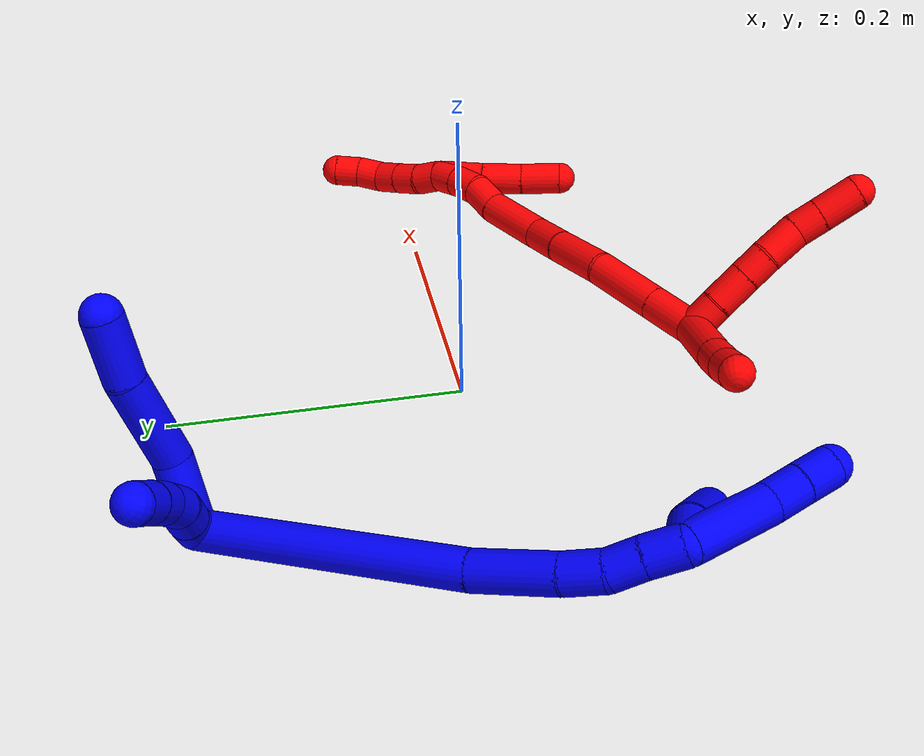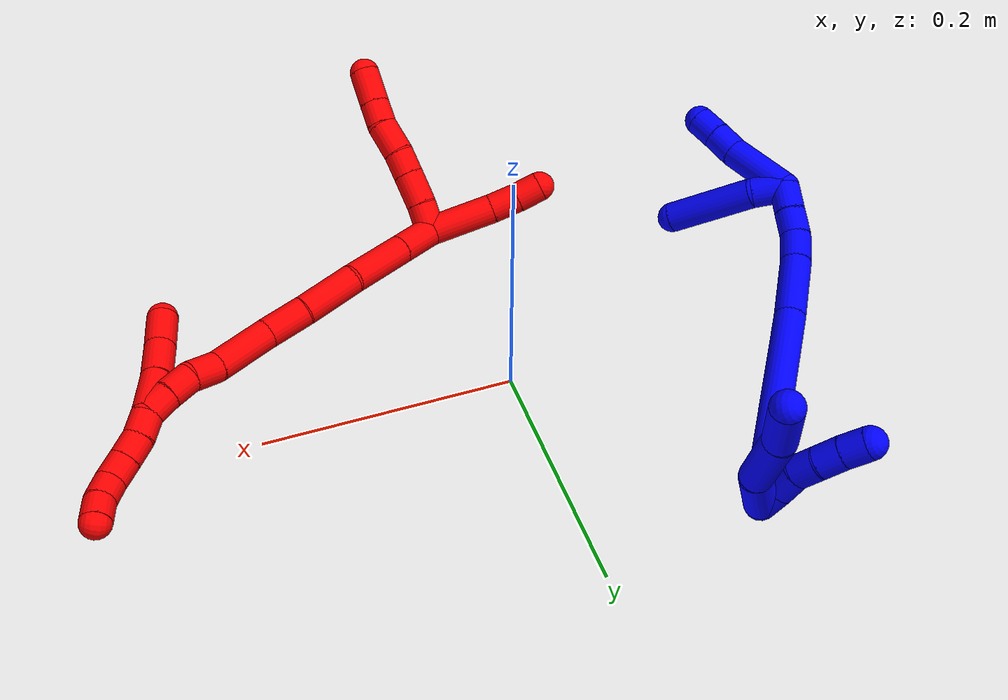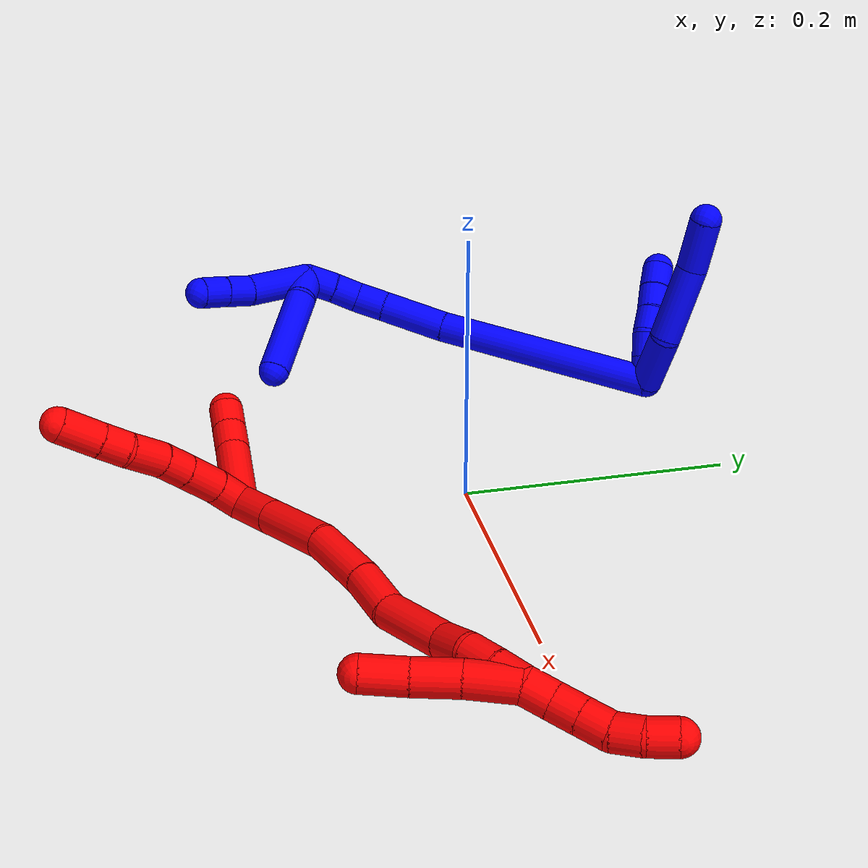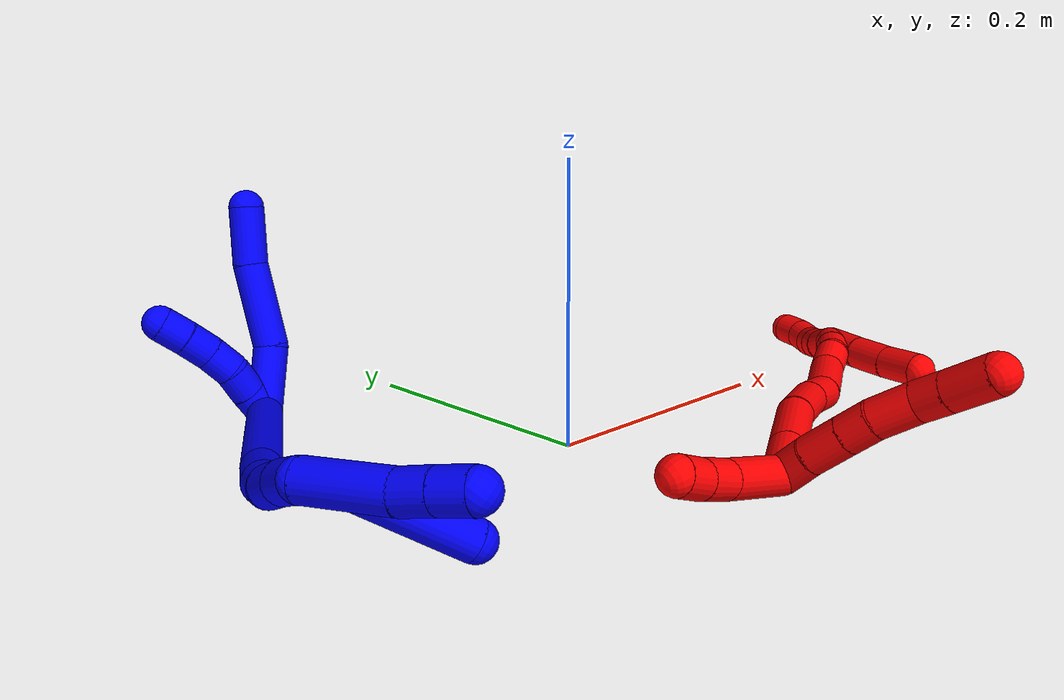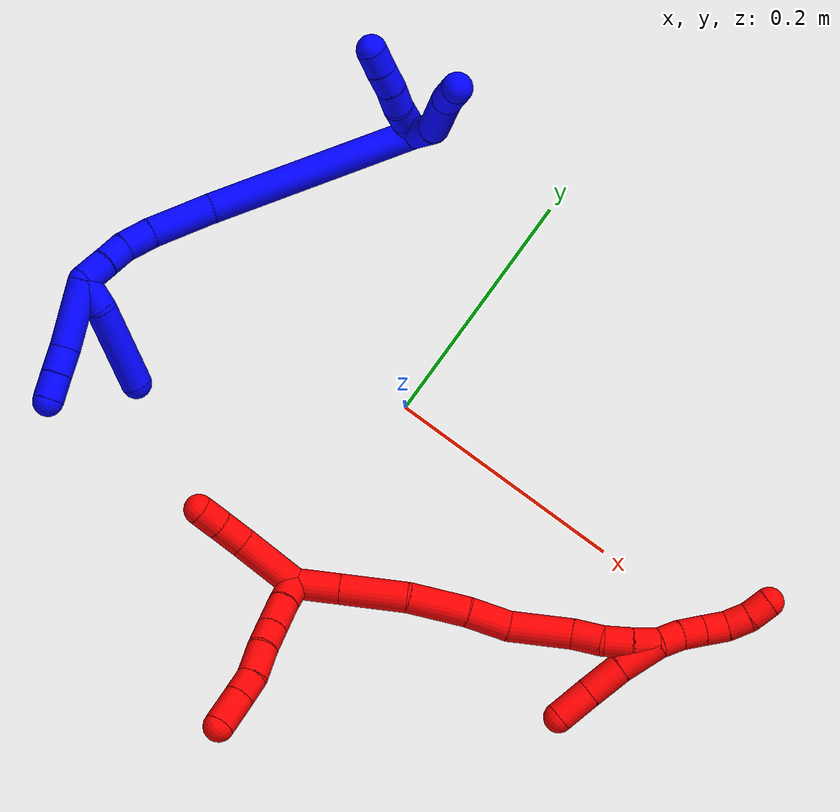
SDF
<sdf version="1.7">
 <world name="default">
  <plugin name="TubeGeneratorPlugin" filename="libtube_generator_plugin.so"/>
  <model name="photoneo_s_sensor">
   <static>1</static>
   <pose>0 0 2 1.57079 1.57079 3.14159</pose>
   <link name="link">
    <inertial><mass>0.1</mass></inertial>
    <sensor name="sensor" type="depth">
     <update_rate>30</update_rate>
     <camera>
      <horizontal_fov>1.22</horizontal_fov>
      <image><width>1920</width><height>1200</height><format>B8G8R8</format></image>
      <clip><near>0.1</near><far>4</far></clip>
      <depth_camera><output>points</output></depth_camera>
     </camera>
     <plugin name="camera_plugin" filename="libgazebo_ros_depth_camera.so">
      <baseline>0.2</baseline>
      <alwaysOn>1</alwaysOn>
      <updateRate>0.0</updateRate>
      <cameraName>camera_ir</cameraName>
      <imageTopicName>/camera/color/image_raw</imageTopicName>
      <cameraInfoTopicName>/camera/color/camera_info</cameraInfoTopicName>
      <depthImageTopicName>/camera/depth/image_raw</depthImageTopicName>
      <depthImageCameraInfoTopicName>/camera/depth/camera_info</depthImageCameraInfoTopicName>
      <pointCloudTopicName>/camera/depth/points</pointCloudTopicName>
      <frameName>fr_optical</frameName>
      <pointCloudCutoff>0.1</pointCloudCutoff>
      <pointCloudCutoffMax>2.0</pointCloudCutoffMax>
      <distortionK1>0</distortionK1>
      <distortionK2>0</distortionK2>
      <distortionK3>0</distortionK3>
      <distortionT1>0</distortionT1>
      <distortionT2>0</distortionT2>
      <CxPrime>0</CxPrime>
      <Cx>0</Cx>
      <Cy>0</Cy>
      <focalLength>0</focalLength>
      <hackBaseline>0</hackBaseline>
     </plugin>
    </sensor>
   </link>
  </model>
  <gravity>0 0 -9.8</gravity>
  <magnetic_field>6e-06 2.3e-05 -4.2e-05</magnetic_field>
  <atmosphere type="adiabatic"/>
  <physics name="default_physics" default="0" type="ode">
   <max_step_size>0.003</max_step_size>
   <real_time_factor>1</real_time_factor>
   <real_time_update_rate>1000</real_time_update_rate>
   <max_contacts>10000</max_contacts>
   <ode>
    <solver>
     <type>quick</type>
     <iters>100</iters>
     <sor>1.3</sor>
     <use_dynamic_moi_rescaling>0</use_dynamic_moi_rescaling>
    </solver>
    <constraints>
     <contact_max_correcting_vel>0</contact_max_correcting_vel>
     <contact_surface_layer>0.001</contact_surface_layer>
     <cfm>0</cfm>
     <erp>0.2</erp>
    </constraints>
   </ode>
  </physics>
  <scene><ambient>0.4 0.4 0.4 1</ambient><background>0.7 0.7 0.7 1</background><shadows>0</shadows></scene>
  <audio><device>default</device></audio>
  <spherical_coordinates>
   <surface_model>EARTH_WGS84</surface_model>
   <latitude_deg>0</latitude_deg>
   <longitude_deg>0</longitude_deg>
   <elevation>0</elevation>
   <heading_deg>0</heading_deg>
  </spherical_coordinates>
  <model name="bin">
   <static>1</static>
   <link name="bottom">
    <collision name="collision-bottom">
     <pose>0 0 -0.01 0 -0 0</pose>
     <geometry><box><size>0.8 0.6 0.02</size></box></geometry>
     <surface>
      <friction><ode><mu>100</mu><mu2>100</mu2></ode></friction>
      <contact><collide_bitmask>65535</collide_bitmask></contact>
     </surface>
    </collision>
   </link>
   <link name="west_wall">
    <collision name="collision-west_wall">
     <pose>-0.41 0 0.1 0 -0 0</pose>
     <geometry><box><size>0.02 0.6 0.2</size></box></geometry>
     <surface>
      <friction><ode><mu>100</mu><mu2>100</mu2></ode></friction>
      <contact><collide_bitmask>65535</collide_bitmask></contact>
     </surface>
    </collision>
   </link>
   <link name="east_wall">
    <collision name="collision-east_wall">
     <pose>0.41 0 0.1 0 -0 0</pose>
     <geometry><box><size>0.02 0.6 0.2</size></box></geometry>
     <surface>
      <friction><ode><mu>100</mu><mu2>100</mu2></ode></friction>
      <contact><collide_bitmask>65535</collide_bitmask></contact>
     </surface>
    </collision>
   </link>
   <link name="south_wall">
    <collision name="collision-south_wall">
     <pose>0 -0.31 0.1 0 -0 0</pose>
     <geometry><box><size>0.8 0.02 0.2</size></box></geometry>
     <surface>
      <friction><ode><mu>100</mu><mu2>100</mu2></ode></friction>
      <contact><collide_bitmask>65535</collide_bitmask></contact>
     </surface>
    </collision>
   </link>
   <link name="north_wall">
    <collision name="collision-north_wall">
     <pose>0 0.31 0.1 0 -0 0</pose>
     <geometry><box><size>0.8 0.02 0.2</size></box></geometry>
     <surface>
      <friction><ode><mu>100</mu><mu2>100</mu2></ode></friction>
      <contact><collide_bitmask>65535</collide_bitmask></contact>
     </surface>
    </collision>
   </link>
  </model>
  <model name="1">
   <static>0</static>
   <link name="1">
    <collision name="collision-cylinder-e_1_2_8">
     <pose>0.019988 -0.003227 0.01248 0.252991 0.998009 0.138402</pose>
     <geometry><cylinder><radius>0.0125</radius><length>0.047569</length></cylinder></geometry>
     <surface>
      <friction><ode><mu>1.16</mu><mu2>1.16</mu2><slip1>0</slip1><slip2>0</slip2></ode></friction>
      <contact><ode><kp>1e+06</kp><kd>1</kd><max_vel>0</max_vel><min_depth>0.001</min_depth></ode></contact>
     </surface>
    </collision>
    <visual name="visual-cylinder-e_1_2_8">
     <pose>0.019988 -0.003227 0.01248 0.252991 0.998009 0.138402</pose>
     <geometry><cylinder><radius>0.0125</radius><length>0.047569</length></cylinder></geometry>
     <material><ambient>0 0 1 1</ambient></material>
    </visual>
    <collision name="collision-cylinder-e_2_8_9">
     <pose>0.058824 -0.011181 0.048353 0.19941 0.668463 0.06945</pose>
     <geometry><cylinder><radius>0.0125</radius><length>0.060821</length></cylinder></geometry>
     <surface>
      <friction><ode><mu>1.16</mu><mu2>1.16</mu2><slip1>0</slip1><slip2>0</slip2></ode></friction>
      <contact><ode><kp>1e+06</kp><kd>1</kd><max_vel>0</max_vel><min_depth>0.001</min_depth></ode></contact>
     </surface>
    </collision>
    <visual name="visual-cylinder-e_2_8_9">
     <pose>0.058824 -0.011181 0.048353 0.19941 0.668463 0.06945</pose>
     <geometry><cylinder><radius>0.0125</radius><length>0.060821</length></cylinder></geometry>
     <material><ambient>0 0 1 1</ambient></material>
    </visual>
    <collision name="collision-cylinder-e_3_9_6">
     <pose>0.092711 -0.020923 0.085219 0.356331 0.807915 0.153649</pose>
     <geometry><cylinder><radius>0.0125</radius><length>0.04161</length></cylinder></geometry>
     <surface>
      <friction><ode><mu>1.16</mu><mu2>1.16</mu2><slip1>0</slip1><slip2>0</slip2></ode></friction>
      <contact><ode><kp>1e+06</kp><kd>1</kd><max_vel>0</max_vel><min_depth>0.001</min_depth></ode></contact>
     </surface>
    </collision>
    <visual name="visual-cylinder-e_3_9_6">
     <pose>0.092711 -0.020923 0.085219 0.356331 0.807915 0.153649</pose>
     <geometry><cylinder><radius>0.0125</radius><length>0.04161</length></cylinder></geometry>
     <material><ambient>0 0 1 1</ambient></material>
    </visual>
    <collision name="collision-cylinder-e_1_2_10">
     <pose>0.001626 -0.004196 0.00893 0.439248 0.16331 0.036532</pose>
     <geometry><cylinder><radius>0.0125</radius><length>0.02</length></cylinder></geometry>
     <surface>
      <friction><ode><mu>1.16</mu><mu2>1.16</mu2><slip1>0</slip1><slip2>0</slip2></ode></friction>
      <contact><ode><kp>1e+06</kp><kd>1</kd><max_vel>0</max_vel><min_depth>0.001</min_depth></ode></contact>
     </surface>
    </collision>
    <visual name="visual-cylinder-e_1_2_10">
     <pose>0.001626 -0.004196 0.00893 0.439248 0.16331 0.036532</pose>
     <geometry><cylinder><radius>0.0125</radius><length>0.02</length></cylinder></geometry>
     <material><ambient>0 0 1 1</ambient></material>
    </visual>
    <collision name="collision-cylinder-e_2_10_11">
     <pose>0.005401 -0.012729 0.026611 0.460101 0.216599 0.050915</pose>
     <geometry><cylinder><radius>0.0125</radius><length>0.02</length></cylinder></geometry>
     <surface>
      <friction><ode><mu>1.16</mu><mu2>1.16</mu2><slip1>0</slip1><slip2>0</slip2></ode></friction>
      <contact><ode><kp>1e+06</kp><kd>1</kd><max_vel>0</max_vel><min_depth>0.001</min_depth></ode></contact>
     </surface>
    </collision>
    <visual name="visual-cylinder-e_2_10_11">
     <pose>0.005401 -0.012729 0.026611 0.460101 0.216599 0.050915</pose>
     <geometry><cylinder><radius>0.0125</radius><length>0.02</length></cylinder></geometry>
     <material><ambient>0 0 1 1</ambient></material>
    </visual>
    <collision name="collision-cylinder-e_3_11_12">
     <pose>0.00765 -0.019532 0.045053 0.249224 0.00998 0.00125</pose>
     <geometry><cylinder><radius>0.0125</radius><length>0.02</length></cylinder></geometry>
     <surface>
      <friction><ode><mu>1.16</mu><mu2>1.16</mu2><slip1>0</slip1><slip2>0</slip2></ode></friction>
      <contact><ode><kp>1e+06</kp><kd>1</kd><max_vel>0</max_vel><min_depth>0.001</min_depth></ode></contact>
     </surface>
    </collision>
    <visual name="visual-cylinder-e_3_11_12">
     <pose>0.00765 -0.019532 0.045053 0.249224 0.00998 0.00125</pose>
     <geometry><cylinder><radius>0.0125</radius><length>0.02</length></cylinder></geometry>
     <material><ambient>0 0 1 1</ambient></material>
    </visual>
    <collision name="collision-cylinder-e_4_12_13">
     <pose>0.006686 -0.025036 0.064211 0.310438 -0.106572 -0.016692</pose>
     <geometry><cylinder><radius>0.0125</radius><length>0.02</length></cylinder></geometry>
     <surface>
      <friction><ode><mu>1.16</mu><mu2>1.16</mu2><slip1>0</slip1><slip2>0</slip2></ode></friction>
      <contact><ode><kp>1e+06</kp><kd>1</kd><max_vel>0</max_vel><min_depth>0.001</min_depth></ode></contact>
     </surface>
    </collision>
    <visual name="visual-cylinder-e_4_12_13">
     <pose>0.006686 -0.025036 0.064211 0.310438 -0.106572 -0.016692</pose>
     <geometry><cylinder><radius>0.0125</radius><length>0.02</length></cylinder></geometry>
     <material><ambient>0 0 1 1</ambient></material>
    </visual>
    <collision name="collision-cylinder-e_5_13_5">
     <pose>0.004186 -0.030569 0.083255 0.254941 -0.144153 -0.018507</pose>
     <geometry><cylinder><radius>0.0125</radius><length>0.02</length></cylinder></geometry>
     <surface>
      <friction><ode><mu>1.16</mu><mu2>1.16</mu2><slip1>0</slip1><slip2>0</slip2></ode></friction>
      <contact><ode><kp>1e+06</kp><kd>1</kd><max_vel>0</max_vel><min_depth>0.001</min_depth></ode></contact>
     </surface>
    </collision>
    <visual name="visual-cylinder-e_5_13_5">
     <pose>0.004186 -0.030569 0.083255 0.254941 -0.144153 -0.018507</pose>
     <geometry><cylinder><radius>0.0125</radius><length>0.02</length></cylinder></geometry>
     <material><ambient>0 0 1 1</ambient></material>
    </visual>
    <collision name="collision-cylinder-e_1_2_14">
     <pose>-0.026183 -0.083651 -0.010709 1.69812 -0.301038 -0.341289</pose>
     <geometry><cylinder><radius>0.0125</radius><length>0.176609</length></cylinder></geometry>
     <surface>
      <friction><ode><mu>1.16</mu><mu2>1.16</mu2><slip1>0</slip1><slip2>0</slip2></ode></friction>
      <contact><ode><kp>1e+06</kp><kd>1</kd><max_vel>0</max_vel><min_depth>0.001</min_depth></ode></contact>
     </surface>
    </collision>
    <visual name="visual-cylinder-e_1_2_14">
     <pose>-0.026183 -0.083651 -0.010709 1.69812 -0.301038 -0.341289</pose>
     <geometry><cylinder><radius>0.0125</radius><length>0.176609</length></cylinder></geometry>
     <material><ambient>0 0 1 1</ambient></material>
    </visual>
    <collision name="collision-cylinder-e_2_14_15">
     <pose>-0.057704 -0.193284 -0.023858 1.66444 -0.201739 -0.221418</pose>
     <geometry><cylinder><radius>0.0125</radius><length>0.053275</length></cylinder></geometry>
     <surface>
      <friction><ode><mu>1.16</mu><mu2>1.16</mu2><slip1>0</slip1><slip2>0</slip2></ode></friction>
      <contact><ode><kp>1e+06</kp><kd>1</kd><max_vel>0</max_vel><min_depth>0.001</min_depth></ode></contact>
     </surface>
    </collision>
    <visual name="visual-cylinder-e_2_14_15">
     <pose>-0.057704 -0.193284 -0.023858 1.66444 -0.201739 -0.221418</pose>
     <geometry><cylinder><radius>0.0125</radius><length>0.053275</length></cylinder></geometry>
     <material><ambient>0 0 1 1</ambient></material>
    </visual>
    <collision name="collision-cylinder-e_3_15_16">
     <pose>-0.064294 -0.231687 -0.02803 1.7093 -0.099552 -0.114362</pose>
     <geometry><cylinder><radius>0.0125</radius><length>0.025204</length></cylinder></geometry>
     <surface>
      <friction><ode><mu>1.16</mu><mu2>1.16</mu2><slip1>0</slip1><slip2>0</slip2></ode></friction>
      <contact><ode><kp>1e+06</kp><kd>1</kd><max_vel>0</max_vel><min_depth>0.001</min_depth></ode></contact>
     </surface>
    </collision>
    <visual name="visual-cylinder-e_3_15_16">
     <pose>-0.064294 -0.231687 -0.02803 1.7093 -0.099552 -0.114362</pose>
     <geometry><cylinder><radius>0.0125</radius><length>0.025204</length></cylinder></geometry>
     <material><ambient>0 0 1 1</ambient></material>
    </visual>
    <collision name="collision-cylinder-e_4_16_17">
     <pose>-0.063622 -0.254371 -0.031713 1.75873 0.182156 0.219784</pose>
     <geometry><cylinder><radius>0.0125</radius><length>0.021249</length></cylinder></geometry>
     <surface>
      <friction><ode><mu>1.16</mu><mu2>1.16</mu2><slip1>0</slip1><slip2>0</slip2></ode></friction>
      <contact><ode><kp>1e+06</kp><kd>1</kd><max_vel>0</max_vel><min_depth>0.001</min_depth></ode></contact>
     </surface>
    </collision>
    <visual name="visual-cylinder-e_4_16_17">
     <pose>-0.063622 -0.254371 -0.031713 1.75873 0.182156 0.219784</pose>
     <geometry><cylinder><radius>0.0125</radius><length>0.021249</length></cylinder></geometry>
     <material><ambient>0 0 1 1</ambient></material>
    </visual>
    <collision name="collision-cylinder-e_5_17_1">
     <pose>-0.060283 -0.276101 -0.036223 1.79031 0.11982 0.149401</pose>
     <geometry><cylinder><radius>0.0125</radius><length>0.023663</length></cylinder></geometry>
     <surface>
      <friction><ode><mu>1.16</mu><mu2>1.16</mu2><slip1>0</slip1><slip2>0</slip2></ode></friction>
      <contact><ode><kp>1e+06</kp><kd>1</kd><max_vel>0</max_vel><min_depth>0.001</min_depth></ode></contact>
     </surface>
    </collision>
    <visual name="visual-cylinder-e_5_17_1">
     <pose>-0.060283 -0.276101 -0.036223 1.79031 0.11982 0.149401</pose>
     <geometry><cylinder><radius>0.0125</radius><length>0.023663</length></cylinder></geometry>
     <material><ambient>0 0 1 1</ambient></material>
    </visual>
    <collision name="collision-cylinder-e_1_1_18">
     <pose>-0.049923 -0.305142 -0.058747 2.41974 0.324432 0.81821</pose>
     <geometry><cylinder><radius>0.0125</radius><length>0.056129</length></cylinder></geometry>
     <surface>
      <friction><ode><mu>1.16</mu><mu2>1.16</mu2><slip1>0</slip1><slip2>0</slip2></ode></friction>
      <contact><ode><kp>1e+06</kp><kd>1</kd><max_vel>0</max_vel><min_depth>0.001</min_depth></ode></contact>
     </surface>
    </collision>
    <visual name="visual-cylinder-e_1_1_18">
     <pose>-0.049923 -0.305142 -0.058747 2.41974 0.324432 0.81821</pose>
     <geometry><cylinder><radius>0.0125</radius><length>0.056129</length></cylinder></geometry>
     <material><ambient>0 0 1 1</ambient></material>
    </visual>
    <collision name="collision-cylinder-e_2_18_19">
     <pose>-0.036635 -0.330568 -0.085312 2.26987 0.400453 0.821885</pose>
     <geometry><cylinder><radius>0.0125</radius><length>0.022271</length></cylinder></geometry>
     <surface>
      <friction><ode><mu>1.16</mu><mu2>1.16</mu2><slip1>0</slip1><slip2>0</slip2></ode></friction>
      <contact><ode><kp>1e+06</kp><kd>1</kd><max_vel>0</max_vel><min_depth>0.001</min_depth></ode></contact>
     </surface>
    </collision>
    <visual name="visual-cylinder-e_2_18_19">
     <pose>-0.036635 -0.330568 -0.085312 2.26987 0.400453 0.821885</pose>
     <geometry><cylinder><radius>0.0125</radius><length>0.022271</length></cylinder></geometry>
     <material><ambient>0 0 1 1</ambient></material>
    </visual>
    <collision name="collision-cylinder-e_3_19_4">
     <pose>-0.028231 -0.345844 -0.098616 2.3052 0.385782 0.828182</pose>
     <geometry><cylinder><radius>0.0125</radius><length>0.0216</length></cylinder></geometry>
     <surface>
      <friction><ode><mu>1.16</mu><mu2>1.16</mu2><slip1>0</slip1><slip2>0</slip2></ode></friction>
      <contact><ode><kp>1e+06</kp><kd>1</kd><max_vel>0</max_vel><min_depth>0.001</min_depth></ode></contact>
     </surface>
    </collision>
    <visual name="visual-cylinder-e_3_19_4">
     <pose>-0.028231 -0.345844 -0.098616 2.3052 0.385782 0.828182</pose>
     <geometry><cylinder><radius>0.0125</radius><length>0.0216</length></cylinder></geometry>
     <material><ambient>0 0 1 1</ambient></material>
    </visual>
    <collision name="collision-cylinder-e_1_1_20">
     <pose>-0.052439 -0.285171 -0.050089 -2.93292 0.507612 -2.37422</pose>
     <geometry><cylinder><radius>0.0125</radius><length>0.026453</length></cylinder></geometry>
     <surface>
      <friction><ode><mu>1.16</mu><mu2>1.16</mu2><slip1>0</slip1><slip2>0</slip2></ode></friction>
      <contact><ode><kp>1e+06</kp><kd>1</kd><max_vel>0</max_vel><min_depth>0.001</min_depth></ode></contact>
     </surface>
    </collision>
    <visual name="visual-cylinder-e_1_1_20">
     <pose>-0.052439 -0.285171 -0.050089 -2.93292 0.507612 -2.37422</pose>
     <geometry><cylinder><radius>0.0125</radius><length>0.026453</length></cylinder></geometry>
     <material><ambient>0 0 1 1</ambient></material>
    </visual>
    <collision name="collision-cylinder-e_2_20_3">
     <pose>-0.038133 -0.276962 -0.096843 -2.97902 0.215883 -1.85233</pose>
     <geometry><cylinder><radius>0.0125</radius><length>0.073547</length></cylinder></geometry>
     <surface>
      <friction><ode><mu>1.16</mu><mu2>1.16</mu2><slip1>0</slip1><slip2>0</slip2></ode></friction>
      <contact><ode><kp>1e+06</kp><kd>1</kd><max_vel>0</max_vel><min_depth>0.001</min_depth></ode></contact>
     </surface>
    </collision>
    <visual name="visual-cylinder-e_2_20_3">
     <pose>-0.038133 -0.276962 -0.096843 -2.97902 0.215883 -1.85233</pose>
     <geometry><cylinder><radius>0.0125</radius><length>0.073547</length></cylinder></geometry>
     <material><ambient>0 0 1 1</ambient></material>
    </visual>
    <collision name="collision-sphere-3">
     <pose>-0.030256 -0.271149 -0.13229 0 -0 0</pose>
     <geometry><sphere><radius>0.0125</radius></sphere></geometry>
     <surface>
      <friction><ode><mu>1.16</mu><mu2>1.16</mu2><slip1>0</slip1><slip2>0</slip2></ode></friction>
      <contact><ode><kp>1e+06</kp><kd>1</kd><max_vel>0</max_vel><min_depth>0.001</min_depth></ode></contact>
     </surface>
    </collision>
    <visual name="visual-sphere-3">
     <pose>-0.030256 -0.271149 -0.13229 0 -0 0</pose>
     <geometry><sphere><radius>0.0125</radius></sphere></geometry>
     <material><ambient>0 0 1 1</ambient></material>
    </visual>
    <collision name="collision-sphere-20">
     <pose>-0.04601 -0.282776 -0.061397 0 -0 0</pose>
     <geometry><sphere><radius>0.0125</radius></sphere></geometry>
     <surface>
      <friction><ode><mu>1.16</mu><mu2>1.16</mu2><slip1>0</slip1><slip2>0</slip2></ode></friction>
      <contact><ode><kp>1e+06</kp><kd>1</kd><max_vel>0</max_vel><min_depth>0.001</min_depth></ode></contact>
     </surface>
    </collision>
    <visual name="visual-sphere-20">
     <pose>-0.04601 -0.282776 -0.061397 0 -0 0</pose>
     <geometry><sphere><radius>0.0125</radius></sphere></geometry>
     <material><ambient>0 0 1 1</ambient></material>
    </visual>
    <collision name="collision-sphere-4">
     <pose>-0.024167 -0.353271 -0.105322 0 -0 0</pose>
     <geometry><sphere><radius>0.0125</radius></sphere></geometry>
     <surface>
      <friction><ode><mu>1.16</mu><mu2>1.16</mu2><slip1>0</slip1><slip2>0</slip2></ode></friction>
      <contact><ode><kp>1e+06</kp><kd>1</kd><max_vel>0</max_vel><min_depth>0.001</min_depth></ode></contact>
     </surface>
    </collision>
    <visual name="visual-sphere-4">
     <pose>-0.024167 -0.353271 -0.105322 0 -0 0</pose>
     <geometry><sphere><radius>0.0125</radius></sphere></geometry>
     <material><ambient>0 0 1 1</ambient></material>
    </visual>
    <collision name="collision-sphere-11">
     <pose>0.00755 -0.017065 0.035362 0 -0 0</pose>
     <geometry><sphere><radius>0.0125</radius></sphere></geometry>
     <surface>
      <friction><ode><mu>1.16</mu><mu2>1.16</mu2><slip1>0</slip1><slip2>0</slip2></ode></friction>
      <contact><ode><kp>1e+06</kp><kd>1</kd><max_vel>0</max_vel><min_depth>0.001</min_depth></ode></contact>
     </surface>
    </collision>
    <visual name="visual-sphere-11">
     <pose>0.00755 -0.017065 0.035362 0 -0 0</pose>
     <geometry><sphere><radius>0.0125</radius></sphere></geometry>
     <material><ambient>0 0 1 1</ambient></material>
    </visual>
    <collision name="collision-sphere-10">
     <pose>0.003252 -0.008392 0.017861 0 -0 0</pose>
     <geometry><sphere><radius>0.0125</radius></sphere></geometry>
     <surface>
      <friction><ode><mu>1.16</mu><mu2>1.16</mu2><slip1>0</slip1><slip2>0</slip2></ode></friction>
      <contact><ode><kp>1e+06</kp><kd>1</kd><max_vel>0</max_vel><min_depth>0.001</min_depth></ode></contact>
     </surface>
    </collision>
    <visual name="visual-sphere-10">
     <pose>0.003252 -0.008392 0.017861 0 -0 0</pose>
     <geometry><sphere><radius>0.0125</radius></sphere></geometry>
     <material><ambient>0 0 1 1</ambient></material>
    </visual>
    <collision name="collision-sphere-6">
     <pose>0.10775 -0.025938 0.098692 0 -0 0</pose>
     <geometry><sphere><radius>0.0125</radius></sphere></geometry>
     <surface>
      <friction><ode><mu>1.16</mu><mu2>1.16</mu2><slip1>0</slip1><slip2>0</slip2></ode></friction>
      <contact><ode><kp>1e+06</kp><kd>1</kd><max_vel>0</max_vel><min_depth>0.001</min_depth></ode></contact>
     </surface>
    </collision>
    <visual name="visual-sphere-6">
     <pose>0.10775 -0.025938 0.098692 0 -0 0</pose>
     <geometry><sphere><radius>0.0125</radius></sphere></geometry>
     <material><ambient>0 0 1 1</ambient></material>
    </visual>
    <collision name="collision-sphere-9">
     <pose>0.077672 -0.015908 0.071745 0 -0 0</pose>
     <geometry><sphere><radius>0.0125</radius></sphere></geometry>
     <surface>
      <friction><ode><mu>1.16</mu><mu2>1.16</mu2><slip1>0</slip1><slip2>0</slip2></ode></friction>
      <contact><ode><kp>1e+06</kp><kd>1</kd><max_vel>0</max_vel><min_depth>0.001</min_depth></ode></contact>
     </surface>
    </collision>
    <visual name="visual-sphere-9">
     <pose>0.077672 -0.015908 0.071745 0 -0 0</pose>
     <geometry><sphere><radius>0.0125</radius></sphere></geometry>
     <material><ambient>0 0 1 1</ambient></material>
    </visual>
    <collision name="collision-sphere-2">
     <geometry><sphere><radius>0.0125</radius></sphere></geometry>
     <surface>
      <friction><ode><mu>1.16</mu><mu2>1.16</mu2><slip1>0</slip1><slip2>0</slip2></ode></friction>
      <contact><ode><kp>1e+06</kp><kd>1</kd><max_vel>0</max_vel><min_depth>0.001</min_depth></ode></contact>
     </surface>
    </collision>
    <visual name="visual-sphere-2">
     <geometry><sphere><radius>0.0125</radius></sphere></geometry>
     <material><ambient>0 0 1 1</ambient></material>
    </visual>
    <collision name="collision-sphere-19">
     <pose>-0.032294 -0.338418 -0.091911 0 -0 0</pose>
     <geometry><sphere><radius>0.0125</radius></sphere></geometry>
     <surface>
      <friction><ode><mu>1.16</mu><mu2>1.16</mu2><slip1>0</slip1><slip2>0</slip2></ode></friction>
      <contact><ode><kp>1e+06</kp><kd>1</kd><max_vel>0</max_vel><min_depth>0.001</min_depth></ode></contact>
     </surface>
    </collision>
    <visual name="visual-sphere-19">
     <pose>-0.032294 -0.338418 -0.091911 0 -0 0</pose>
     <geometry><sphere><radius>0.0125</radius></sphere></geometry>
     <material><ambient>0 0 1 1</ambient></material>
    </visual>
    <collision name="collision-sphere-8">
     <pose>0.039977 -0.006453 0.024961 0 -0 0</pose>
     <geometry><sphere><radius>0.0125</radius></sphere></geometry>
     <surface>
      <friction><ode><mu>1.16</mu><mu2>1.16</mu2><slip1>0</slip1><slip2>0</slip2></ode></friction>
      <contact><ode><kp>1e+06</kp><kd>1</kd><max_vel>0</max_vel><min_depth>0.001</min_depth></ode></contact>
     </surface>
    </collision>
    <visual name="visual-sphere-8">
     <pose>0.039977 -0.006453 0.024961 0 -0 0</pose>
     <geometry><sphere><radius>0.0125</radius></sphere></geometry>
     <material><ambient>0 0 1 1</ambient></material>
    </visual>
    <collision name="collision-sphere-12">
     <pose>0.007749 -0.021998 0.054743 0 -0 0</pose>
     <geometry><sphere><radius>0.0125</radius></sphere></geometry>
     <surface>
      <friction><ode><mu>1.16</mu><mu2>1.16</mu2><slip1>0</slip1><slip2>0</slip2></ode></friction>
      <contact><ode><kp>1e+06</kp><kd>1</kd><max_vel>0</max_vel><min_depth>0.001</min_depth></ode></contact>
     </surface>
    </collision>
    <visual name="visual-sphere-12">
     <pose>0.007749 -0.021998 0.054743 0 -0 0</pose>
     <geometry><sphere><radius>0.0125</radius></sphere></geometry>
     <material><ambient>0 0 1 1</ambient></material>
    </visual>
    <collision name="collision-sphere-13">
     <pose>0.005622 -0.028073 0.073679 0 -0 0</pose>
     <geometry><sphere><radius>0.0125</radius></sphere></geometry>
     <surface>
      <friction><ode><mu>1.16</mu><mu2>1.16</mu2><slip1>0</slip1><slip2>0</slip2></ode></friction>
      <contact><ode><kp>1e+06</kp><kd>1</kd><max_vel>0</max_vel><min_depth>0.001</min_depth></ode></contact>
     </surface>
    </collision>
    <visual name="visual-sphere-13">
     <pose>0.005622 -0.028073 0.073679 0 -0 0</pose>
     <geometry><sphere><radius>0.0125</radius></sphere></geometry>
     <material><ambient>0 0 1 1</ambient></material>
    </visual>
    <collision name="collision-sphere-5">
     <pose>0.002749 -0.033064 0.092832 0 -0 0</pose>
     <geometry><sphere><radius>0.0125</radius></sphere></geometry>
     <surface>
      <friction><ode><mu>1.16</mu><mu2>1.16</mu2><slip1>0</slip1><slip2>0</slip2></ode></friction>
      <contact><ode><kp>1e+06</kp><kd>1</kd><max_vel>0</max_vel><min_depth>0.001</min_depth></ode></contact>
     </surface>
    </collision>
    <visual name="visual-sphere-5">
     <pose>0.002749 -0.033064 0.092832 0 -0 0</pose>
     <geometry><sphere><radius>0.0125</radius></sphere></geometry>
     <material><ambient>0 0 1 1</ambient></material>
    </visual>
    <collision name="collision-sphere-14">
     <pose>-0.052367 -0.167301 -0.021418 0 -0 0</pose>
     <geometry><sphere><radius>0.0125</radius></sphere></geometry>
     <surface>
      <friction><ode><mu>1.16</mu><mu2>1.16</mu2><slip1>0</slip1><slip2>0</slip2></ode></friction>
      <contact><ode><kp>1e+06</kp><kd>1</kd><max_vel>0</max_vel><min_depth>0.001</min_depth></ode></contact>
     </surface>
    </collision>
    <visual name="visual-sphere-14">
     <pose>-0.052367 -0.167301 -0.021418 0 -0 0</pose>
     <geometry><sphere><radius>0.0125</radius></sphere></geometry>
     <material><ambient>0 0 1 1</ambient></material>
    </visual>
    <collision name="collision-sphere-15">
     <pose>-0.063042 -0.219267 -0.026298 0 -0 0</pose>
     <geometry><sphere><radius>0.0125</radius></sphere></geometry>
     <surface>
      <friction><ode><mu>1.16</mu><mu2>1.16</mu2><slip1>0</slip1><slip2>0</slip2></ode></friction>
      <contact><ode><kp>1e+06</kp><kd>1</kd><max_vel>0</max_vel><min_depth>0.001</min_depth></ode></contact>
     </surface>
    </collision>
    <visual name="visual-sphere-15">
     <pose>-0.063042 -0.219267 -0.026298 0 -0 0</pose>
     <geometry><sphere><radius>0.0125</radius></sphere></geometry>
     <material><ambient>0 0 1 1</ambient></material>
    </visual>
    <collision name="collision-sphere-16">
     <pose>-0.065547 -0.244106 -0.029761 0 -0 0</pose>
     <geometry><sphere><radius>0.0125</radius></sphere></geometry>
     <surface>
      <friction><ode><mu>1.16</mu><mu2>1.16</mu2><slip1>0</slip1><slip2>0</slip2></ode></friction>
      <contact><ode><kp>1e+06</kp><kd>1</kd><max_vel>0</max_vel><min_depth>0.001</min_depth></ode></contact>
     </surface>
    </collision>
    <visual name="visual-sphere-16">
     <pose>-0.065547 -0.244106 -0.029761 0 -0 0</pose>
     <geometry><sphere><radius>0.0125</radius></sphere></geometry>
     <material><ambient>0 0 1 1</ambient></material>
    </visual>
    <collision name="collision-sphere-17">
     <pose>-0.061697 -0.264636 -0.033665 0 -0 0</pose>
     <geometry><sphere><radius>0.0125</radius></sphere></geometry>
     <surface>
      <friction><ode><mu>1.16</mu><mu2>1.16</mu2><slip1>0</slip1><slip2>0</slip2></ode></friction>
      <contact><ode><kp>1e+06</kp><kd>1</kd><max_vel>0</max_vel><min_depth>0.001</min_depth></ode></contact>
     </surface>
    </collision>
    <visual name="visual-sphere-17">
     <pose>-0.061697 -0.264636 -0.033665 0 -0 0</pose>
     <geometry><sphere><radius>0.0125</radius></sphere></geometry>
     <material><ambient>0 0 1 1</ambient></material>
    </visual>
    <collision name="collision-sphere-1">
     <pose>-0.058869 -0.287565 -0.038781 0 -0 0</pose>
     <geometry><sphere><radius>0.0125</radius></sphere></geometry>
     <surface>
      <friction><ode><mu>1.16</mu><mu2>1.16</mu2><slip1>0</slip1><slip2>0</slip2></ode></friction>
      <contact><ode><kp>1e+06</kp><kd>1</kd><max_vel>0</max_vel><min_depth>0.001</min_depth></ode></contact>
     </surface>
    </collision>
    <visual name="visual-sphere-1">
     <pose>-0.058869 -0.287565 -0.038781 0 -0 0</pose>
     <geometry><sphere><radius>0.0125</radius></sphere></geometry>
     <material><ambient>0 0 1 1</ambient></material>
    </visual>
    <collision name="collision-sphere-18">
     <pose>-0.040976 -0.322719 -0.078713 0 -0 0</pose>
     <geometry><sphere><radius>0.0125</radius></sphere></geometry>
     <surface>
      <friction><ode><mu>1.16</mu><mu2>1.16</mu2><slip1>0</slip1><slip2>0</slip2></ode></friction>
      <contact><ode><kp>1e+06</kp><kd>1</kd><max_vel>0</max_vel><min_depth>0.001</min_depth></ode></contact>
     </surface>
    </collision>
    <visual name="visual-sphere-18">
     <pose>-0.040976 -0.322719 -0.078713 0 -0 0</pose>
     <geometry><sphere><radius>0.0125</radius></sphere></geometry>
     <material><ambient>0 0 1 1</ambient></material>
    </visual>
    <inertial>
     <pose>-0.015493 -0.141689 -0.012711 0 -0 0</pose>
     <mass>0.75</mass>
     <inertia>
      <ixx>0.000314</ixx>
      <ixy>0</ixy>
      <ixz>0</ixz>
      <iyy>-0.000161</iyy>
      <iyz>0</iyz>
      <izz>0.000574</izz>
     </inertia>
    </inertial>
   </link>
   <pose>-0.126089 0.183761 0.012027 -0.607426 -0.737953 -0.023255</pose>
  </model>
  <model name="2">
   <static>0</static>
   <link name="2">
    <collision name="collision-cylinder-e_1_2_8">
     <pose>-0.007378 0.007824 0.005245 -0.980261 -0.664457 0.364095</pose>
     <geometry><cylinder><radius>0.0125</radius><length>0.023931</length></cylinder></geometry>
     <surface>
      <friction><ode><mu>1.16</mu><mu2>1.16</mu2><slip1>0</slip1><slip2>0</slip2></ode></friction>
      <contact><ode><kp>1e+06</kp><kd>1</kd><max_vel>0</max_vel><min_depth>0.001</min_depth></ode></contact>
     </surface>
    </collision>
    <visual name="visual-cylinder-e_1_2_8">
     <pose>-0.007378 0.007824 0.005245 -0.980261 -0.664457 0.364095</pose>
     <geometry><cylinder><radius>0.0125</radius><length>0.023931</length></cylinder></geometry>
     <material><ambient>1 0 0 1</ambient></material>
    </visual>
    <collision name="collision-cylinder-e_2_8_9">
     <pose>-0.023645 0.023575 0.017359 -0.856748 -0.703025 0.33187</pose>
     <geometry><cylinder><radius>0.0125</radius><length>0.027498</length></cylinder></geometry>
     <surface>
      <friction><ode><mu>1.16</mu><mu2>1.16</mu2><slip1>0</slip1><slip2>0</slip2></ode></friction>
      <contact><ode><kp>1e+06</kp><kd>1</kd><max_vel>0</max_vel><min_depth>0.001</min_depth></ode></contact>
     </surface>
    </collision>
    <visual name="visual-cylinder-e_2_8_9">
     <pose>-0.023645 0.023575 0.017359 -0.856748 -0.703025 0.33187</pose>
     <geometry><cylinder><radius>0.0125</radius><length>0.027498</length></cylinder></geometry>
     <material><ambient>1 0 0 1</ambient></material>
    </visual>
    <collision name="collision-cylinder-e_3_9_10">
     <pose>-0.039159 0.037291 0.029331 -0.84837 -0.709403 0.331447</pose>
     <geometry><cylinder><radius>0.0125</radius><length>0.02034</length></cylinder></geometry>
     <surface>
      <friction><ode><mu>1.16</mu><mu2>1.16</mu2><slip1>0</slip1><slip2>0</slip2></ode></friction>
      <contact><ode><kp>1e+06</kp><kd>1</kd><max_vel>0</max_vel><min_depth>0.001</min_depth></ode></contact>
     </surface>
    </collision>
    <visual name="visual-cylinder-e_3_9_10">
     <pose>-0.039159 0.037291 0.029331 -0.84837 -0.709403 0.331447</pose>
     <geometry><cylinder><radius>0.0125</radius><length>0.02034</length></cylinder></geometry>
     <material><ambient>1 0 0 1</ambient></material>
    </visual>
    <collision name="collision-cylinder-e_4_10_11">
     <pose>-0.055392 0.04919 0.042228 -0.664783 -0.770235 0.278054</pose>
     <geometry><cylinder><radius>0.0125</radius><length>0.027598</length></cylinder></geometry>
     <surface>
      <friction><ode><mu>1.16</mu><mu2>1.16</mu2><slip1>0</slip1><slip2>0</slip2></ode></friction>
      <contact><ode><kp>1e+06</kp><kd>1</kd><max_vel>0</max_vel><min_depth>0.001</min_depth></ode></contact>
     </surface>
    </collision>
    <visual name="visual-cylinder-e_4_10_11">
     <pose>-0.055392 0.04919 0.042228 -0.664783 -0.770235 0.278054</pose>
     <geometry><cylinder><radius>0.0125</radius><length>0.027598</length></cylinder></geometry>
     <material><ambient>1 0 0 1</ambient></material>
    </visual>
    <collision name="collision-cylinder-e_5_11_12">
     <pose>-0.073027 0.060206 0.053758 -0.920126 -0.915763 0.479029</pose>
     <geometry><cylinder><radius>0.0125</radius><length>0.020244</length></cylinder></geometry>
     <surface>
      <friction><ode><mu>1.16</mu><mu2>1.16</mu2><slip1>0</slip1><slip2>0</slip2></ode></friction>
      <contact><ode><kp>1e+06</kp><kd>1</kd><max_vel>0</max_vel><min_depth>0.001</min_depth></ode></contact>
     </surface>
    </collision>
    <visual name="visual-cylinder-e_5_11_12">
     <pose>-0.073027 0.060206 0.053758 -0.920126 -0.915763 0.479029</pose>
     <geometry><cylinder><radius>0.0125</radius><length>0.020244</length></cylinder></geometry>
     <material><ambient>1 0 0 1</ambient></material>
    </visual>
    <collision name="collision-cylinder-e_6_12_6">
     <pose>-0.092992 0.072747 0.062976 -0.94796 -0.903797 0.488077</pose>
     <geometry><cylinder><radius>0.0125</radius><length>0.03039</length></cylinder></geometry>
     <surface>
      <friction><ode><mu>1.16</mu><mu2>1.16</mu2><slip1>0</slip1><slip2>0</slip2></ode></friction>
      <contact><ode><kp>1e+06</kp><kd>1</kd><max_vel>0</max_vel><min_depth>0.001</min_depth></ode></contact>
     </surface>
    </collision>
    <visual name="visual-cylinder-e_6_12_6">
     <pose>-0.092992 0.072747 0.062976 -0.94796 -0.903797 0.488077</pose>
     <geometry><cylinder><radius>0.0125</radius><length>0.03039</length></cylinder></geometry>
     <material><ambient>1 0 0 1</ambient></material>
    </visual>
    <collision name="collision-cylinder-e_1_2_13">
     <pose>-0.00381 0.01335 -0.023746 -2.62941 -0.138953 0.519526</pose>
     <geometry><cylinder><radius>0.0125</radius><length>0.055013</length></cylinder></geometry>
     <surface>
      <friction><ode><mu>1.16</mu><mu2>1.16</mu2><slip1>0</slip1><slip2>0</slip2></ode></friction>
      <contact><ode><kp>1e+06</kp><kd>1</kd><max_vel>0</max_vel><min_depth>0.001</min_depth></ode></contact>
     </surface>
    </collision>
    <visual name="visual-cylinder-e_1_2_13">
     <pose>-0.00381 0.01335 -0.023746 -2.62941 -0.138953 0.519526</pose>
     <geometry><cylinder><radius>0.0125</radius><length>0.055013</length></cylinder></geometry>
     <material><ambient>1 0 0 1</ambient></material>
    </visual>
    <collision name="collision-cylinder-e_2_13_14">
     <pose>-0.009313 0.033084 -0.057278 -2.56366 -0.143916 0.475753</pose>
     <geometry><cylinder><radius>0.0125</radius><length>0.023612</length></cylinder></geometry>
     <surface>
      <friction><ode><mu>1.16</mu><mu2>1.16</mu2><slip1>0</slip1><slip2>0</slip2></ode></friction>
      <contact><ode><kp>1e+06</kp><kd>1</kd><max_vel>0</max_vel><min_depth>0.001</min_depth></ode></contact>
     </surface>
    </collision>
    <visual name="visual-cylinder-e_2_13_14">
     <pose>-0.009313 0.033084 -0.057278 -2.56366 -0.143916 0.475753</pose>
     <geometry><cylinder><radius>0.0125</radius><length>0.023612</length></cylinder></geometry>
     <material><ambient>1 0 0 1</ambient></material>
    </visual>
    <collision name="collision-cylinder-e_3_14_5">
     <pose>-0.01245 0.045979 -0.075414 -2.47925 -0.135554 0.389832</pose>
     <geometry><cylinder><radius>0.0125</radius><length>0.021375</length></cylinder></geometry>
     <surface>
      <friction><ode><mu>1.16</mu><mu2>1.16</mu2><slip1>0</slip1><slip2>0</slip2></ode></friction>
      <contact><ode><kp>1e+06</kp><kd>1</kd><max_vel>0</max_vel><min_depth>0.001</min_depth></ode></contact>
     </surface>
    </collision>
    <visual name="visual-cylinder-e_3_14_5">
     <pose>-0.01245 0.045979 -0.075414 -2.47925 -0.135554 0.389832</pose>
     <geometry><cylinder><radius>0.0125</radius><length>0.021375</length></cylinder></geometry>
     <material><ambient>1 0 0 1</ambient></material>
    </visual>
    <collision name="collision-cylinder-e_1_2_15">
     <pose>0.012448 -0.003376 0.013621 0.242984 0.72558 0.092625</pose>
     <geometry><cylinder><radius>0.0125</radius><length>0.037517</length></cylinder></geometry>
     <surface>
      <friction><ode><mu>1.16</mu><mu2>1.16</mu2><slip1>0</slip1><slip2>0</slip2></ode></friction>
      <contact><ode><kp>1e+06</kp><kd>1</kd><max_vel>0</max_vel><min_depth>0.001</min_depth></ode></contact>
     </surface>
    </collision>
    <visual name="visual-cylinder-e_1_2_15">
     <pose>0.012448 -0.003376 0.013621 0.242984 0.72558 0.092625</pose>
     <geometry><cylinder><radius>0.0125</radius><length>0.037517</length></cylinder></geometry>
     <material><ambient>1 0 0 1</ambient></material>
    </visual>
    <collision name="collision-cylinder-e_2_15_16">
     <pose>0.043171 -0.011727 0.047338 0.242657 0.72324 0.092174</pose>
     <geometry><cylinder><radius>0.0125</radius><length>0.055228</length></cylinder></geometry>
     <surface>
      <friction><ode><mu>1.16</mu><mu2>1.16</mu2><slip1>0</slip1><slip2>0</slip2></ode></friction>
      <contact><ode><kp>1e+06</kp><kd>1</kd><max_vel>0</max_vel><min_depth>0.001</min_depth></ode></contact>
     </surface>
    </collision>
    <visual name="visual-cylinder-e_2_15_16">
     <pose>0.043171 -0.011727 0.047338 0.242657 0.72324 0.092174</pose>
     <geometry><cylinder><radius>0.0125</radius><length>0.055228</length></cylinder></geometry>
     <material><ambient>1 0 0 1</ambient></material>
    </visual>
    <collision name="collision-cylinder-e_3_16_17">
     <pose>0.075075 -0.025684 0.08595 0.451667 0.584901 0.138129</pose>
     <geometry><cylinder><radius>0.0125</radius><length>0.049369</length></cylinder></geometry>
     <surface>
      <friction><ode><mu>1.16</mu><mu2>1.16</mu2><slip1>0</slip1><slip2>0</slip2></ode></friction>
      <contact><ode><kp>1e+06</kp><kd>1</kd><max_vel>0</max_vel><min_depth>0.001</min_depth></ode></contact>
     </surface>
    </collision>
    <visual name="visual-cylinder-e_3_16_17">
     <pose>0.075075 -0.025684 0.08595 0.451667 0.584901 0.138129</pose>
     <geometry><cylinder><radius>0.0125</radius><length>0.049369</length></cylinder></geometry>
     <material><ambient>1 0 0 1</ambient></material>
    </visual>
    <collision name="collision-cylinder-e_4_17_18">
     <pose>0.096899 -0.042298 0.11834 0.502848 0.477643 0.124911</pose>
     <geometry><cylinder><radius>0.0125</radius><length>0.035657</length></cylinder></geometry>
     <surface>
      <friction><ode><mu>1.16</mu><mu2>1.16</mu2><slip1>0</slip1><slip2>0</slip2></ode></friction>
      <contact><ode><kp>1e+06</kp><kd>1</kd><max_vel>0</max_vel><min_depth>0.001</min_depth></ode></contact>
     </surface>
    </collision>
    <visual name="visual-cylinder-e_4_17_18">
     <pose>0.096899 -0.042298 0.11834 0.502848 0.477643 0.124911</pose>
     <geometry><cylinder><radius>0.0125</radius><length>0.035657</length></cylinder></geometry>
     <material><ambient>1 0 0 1</ambient></material>
    </visual>
    <collision name="collision-cylinder-e_5_18_19">
     <pose>0.122404 -0.055732 0.150947 0.300422 0.723093 0.114348</pose>
     <geometry><cylinder><radius>0.0125</radius><length>0.052316</length></cylinder></geometry>
     <surface>
      <friction><ode><mu>1.16</mu><mu2>1.16</mu2><slip1>0</slip1><slip2>0</slip2></ode></friction>
      <contact><ode><kp>1e+06</kp><kd>1</kd><max_vel>0</max_vel><min_depth>0.001</min_depth></ode></contact>
     </surface>
    </collision>
    <visual name="visual-cylinder-e_5_18_19">
     <pose>0.122404 -0.055732 0.150947 0.300422 0.723093 0.114348</pose>
     <geometry><cylinder><radius>0.0125</radius><length>0.052316</length></cylinder></geometry>
     <material><ambient>1 0 0 1</ambient></material>
    </visual>
    <collision name="collision-cylinder-e_6_19_20">
     <pose>0.147139 -0.062046 0.17991 0.04984 0.62741 0.016172</pose>
     <geometry><cylinder><radius>0.0125</radius><length>0.025301</length></cylinder></geometry>
     <surface>
      <friction><ode><mu>1.16</mu><mu2>1.16</mu2><slip1>0</slip1><slip2>0</slip2></ode></friction>
      <contact><ode><kp>1e+06</kp><kd>1</kd><max_vel>0</max_vel><min_depth>0.001</min_depth></ode></contact>
     </surface>
    </collision>
    <visual name="visual-cylinder-e_6_19_20">
     <pose>0.147139 -0.062046 0.17991 0.04984 0.62741 0.016172</pose>
     <geometry><cylinder><radius>0.0125</radius><length>0.025301</length></cylinder></geometry>
     <material><ambient>1 0 0 1</ambient></material>
    </visual>
    <collision name="collision-cylinder-e_7_20_21">
     <pose>0.162553 -0.065907 0.197802 0.412242 0.762366 0.16721</pose>
     <geometry><cylinder><radius>0.0125</radius><length>0.023131</length></cylinder></geometry>
     <surface>
      <friction><ode><mu>1.16</mu><mu2>1.16</mu2><slip1>0</slip1><slip2>0</slip2></ode></friction>
      <contact><ode><kp>1e+06</kp><kd>1</kd><max_vel>0</max_vel><min_depth>0.001</min_depth></ode></contact>
     </surface>
    </collision>
    <visual name="visual-cylinder-e_7_20_21">
     <pose>0.162553 -0.065907 0.197802 0.412242 0.762366 0.16721</pose>
     <geometry><cylinder><radius>0.0125</radius><length>0.023131</length></cylinder></geometry>
     <material><ambient>1 0 0 1</ambient></material>
    </visual>
    <collision name="collision-cylinder-e_8_21_1">
     <pose>0.178162 -0.073119 0.211975 0.535279 0.788861 0.2273</pose>
     <geometry><cylinder><radius>0.0125</radius><length>0.02148</length></cylinder></geometry>
     <surface>
      <friction><ode><mu>1.16</mu><mu2>1.16</mu2><slip1>0</slip1><slip2>0</slip2></ode></friction>
      <contact><ode><kp>1e+06</kp><kd>1</kd><max_vel>0</max_vel><min_depth>0.001</min_depth></ode></contact>
     </surface>
    </collision>
    <visual name="visual-cylinder-e_8_21_1">
     <pose>0.178162 -0.073119 0.211975 0.535279 0.788861 0.2273</pose>
     <geometry><cylinder><radius>0.0125</radius><length>0.02148</length></cylinder></geometry>
     <material><ambient>1 0 0 1</ambient></material>
    </visual>
    <collision name="collision-cylinder-e_1_1_22">
     <pose>0.167957 -0.074122 0.216201 -2.24501 -1.36844 2.07606</pose>
     <geometry><cylinder><radius>0.0125</radius><length>0.036393</length></cylinder></geometry>
     <surface>
      <friction><ode><mu>1.16</mu><mu2>1.16</mu2><slip1>0</slip1><slip2>0</slip2></ode></friction>
      <contact><ode><kp>1e+06</kp><kd>1</kd><max_vel>0</max_vel><min_depth>0.001</min_depth></ode></contact>
     </surface>
    </collision>
    <visual name="visual-cylinder-e_1_1_22">
     <pose>0.167957 -0.074122 0.216201 -2.24501 -1.36844 2.07606</pose>
     <geometry><cylinder><radius>0.0125</radius><length>0.036393</length></cylinder></geometry>
     <material><ambient>1 0 0 1</ambient></material>
    </visual>
    <collision name="collision-cylinder-e_2_22_23">
     <pose>0.134154 -0.069373 0.213431 -1.82294 -1.44911 1.70327</pose>
     <geometry><cylinder><radius>0.0125</radius><length>0.032193</length></cylinder></geometry>
     <surface>
      <friction><ode><mu>1.16</mu><mu2>1.16</mu2><slip1>0</slip1><slip2>0</slip2></ode></friction>
      <contact><ode><kp>1e+06</kp><kd>1</kd><max_vel>0</max_vel><min_depth>0.001</min_depth></ode></contact>
     </surface>
    </collision>
    <visual name="visual-cylinder-e_2_22_23">
     <pose>0.134154 -0.069373 0.213431 -1.82294 -1.44911 1.70327</pose>
     <geometry><cylinder><radius>0.0125</radius><length>0.032193</length></cylinder></geometry>
     <material><ambient>1 0 0 1</ambient></material>
    </visual>
    <collision name="collision-cylinder-e_3_23_4">
     <pose>0.102675 -0.064951 0.212861 -1.60327 -1.40891 1.44104</pose>
     <geometry><cylinder><radius>0.0125</radius><length>0.031414</length></cylinder></geometry>
     <surface>
      <friction><ode><mu>1.16</mu><mu2>1.16</mu2><slip1>0</slip1><slip2>0</slip2></ode></friction>
      <contact><ode><kp>1e+06</kp><kd>1</kd><max_vel>0</max_vel><min_depth>0.001</min_depth></ode></contact>
     </surface>
    </collision>
    <visual name="visual-cylinder-e_3_23_4">
     <pose>0.102675 -0.064951 0.212861 -1.60327 -1.40891 1.44104</pose>
     <geometry><cylinder><radius>0.0125</radius><length>0.031414</length></cylinder></geometry>
     <material><ambient>1 0 0 1</ambient></material>
    </visual>
    <collision name="collision-cylinder-e_1_1_24">
     <pose>0.194094 -0.082063 0.220737 1.15372 0.981215 0.669031</pose>
     <geometry><cylinder><radius>0.0125</radius><length>0.02</length></cylinder></geometry>
     <surface>
      <friction><ode><mu>1.16</mu><mu2>1.16</mu2><slip1>0</slip1><slip2>0</slip2></ode></friction>
      <contact><ode><kp>1e+06</kp><kd>1</kd><max_vel>0</max_vel><min_depth>0.001</min_depth></ode></contact>
     </surface>
    </collision>
    <visual name="visual-cylinder-e_1_1_24">
     <pose>0.194094 -0.082063 0.220737 1.15372 0.981215 0.669031</pose>
     <geometry><cylinder><radius>0.0125</radius><length>0.02</length></cylinder></geometry>
     <material><ambient>1 0 0 1</ambient></material>
    </visual>
    <collision name="collision-cylinder-e_2_24_25">
     <pose>0.210512 -0.09133 0.227085 0.796015 0.945312 0.423513</pose>
     <geometry><cylinder><radius>0.0125</radius><length>0.02</length></cylinder></geometry>
     <surface>
      <friction><ode><mu>1.16</mu><mu2>1.16</mu2><slip1>0</slip1><slip2>0</slip2></ode></friction>
      <contact><ode><kp>1e+06</kp><kd>1</kd><max_vel>0</max_vel><min_depth>0.001</min_depth></ode></contact>
     </surface>
    </collision>
    <visual name="visual-cylinder-e_2_24_25">
     <pose>0.210512 -0.09133 0.227085 0.796015 0.945312 0.423513</pose>
     <geometry><cylinder><radius>0.0125</radius><length>0.02</length></cylinder></geometry>
     <material><ambient>1 0 0 1</ambient></material>
    </visual>
    <collision name="collision-cylinder-e_3_25_26">
     <pose>0.226711 -0.099557 0.235443 0.759081 0.942768 0.401157</pose>
     <geometry><cylinder><radius>0.0125</radius><length>0.02</length></cylinder></geometry>
     <surface>
      <friction><ode><mu>1.16</mu><mu2>1.16</mu2><slip1>0</slip1><slip2>0</slip2></ode></friction>
      <contact><ode><kp>1e+06</kp><kd>1</kd><max_vel>0</max_vel><min_depth>0.001</min_depth></ode></contact>
     </surface>
    </collision>
    <visual name="visual-cylinder-e_3_25_26">
     <pose>0.226711 -0.099557 0.235443 0.759081 0.942768 0.401157</pose>
     <geometry><cylinder><radius>0.0125</radius><length>0.02</length></cylinder></geometry>
     <material><ambient>1 0 0 1</ambient></material>
    </visual>
    <collision name="collision-cylinder-e_4_26_27">
     <pose>0.244235 -0.10476 0.242818 0.356565 1.23225 0.253813</pose>
     <geometry><cylinder><radius>0.0125</radius><length>0.02</length></cylinder></geometry>
     <surface>
      <friction><ode><mu>1.16</mu><mu2>1.16</mu2><slip1>0</slip1><slip2>0</slip2></ode></friction>
      <contact><ode><kp>1e+06</kp><kd>1</kd><max_vel>0</max_vel><min_depth>0.001</min_depth></ode></contact>
     </surface>
    </collision>
    <visual name="visual-cylinder-e_4_26_27">
     <pose>0.244235 -0.10476 0.242818 0.356565 1.23225 0.253813</pose>
     <geometry><cylinder><radius>0.0125</radius><length>0.02</length></cylinder></geometry>
     <material><ambient>1 0 0 1</ambient></material>
    </visual>
    <collision name="collision-cylinder-e_5_27_3">
     <pose>0.263606 -0.106786 0.24663 0.891142 1.45918 0.807237</pose>
     <geometry><cylinder><radius>0.0125</radius><length>0.02</length></cylinder></geometry>
     <surface>
      <friction><ode><mu>1.16</mu><mu2>1.16</mu2><slip1>0</slip1><slip2>0</slip2></ode></friction>
      <contact><ode><kp>1e+06</kp><kd>1</kd><max_vel>0</max_vel><min_depth>0.001</min_depth></ode></contact>
     </surface>
    </collision>
    <visual name="visual-cylinder-e_5_27_3">
     <pose>0.263606 -0.106786 0.24663 0.891142 1.45918 0.807237</pose>
     <geometry><cylinder><radius>0.0125</radius><length>0.02</length></cylinder></geometry>
     <material><ambient>1 0 0 1</ambient></material>
    </visual>
    <collision name="collision-sphere-3">
     <pose>0.273543 -0.107652 0.24733 0 -0 0</pose>
     <geometry><sphere><radius>0.0125</radius></sphere></geometry>
     <surface>
      <friction><ode><mu>1.16</mu><mu2>1.16</mu2><slip1>0</slip1><slip2>0</slip2></ode></friction>
      <contact><ode><kp>1e+06</kp><kd>1</kd><max_vel>0</max_vel><min_depth>0.001</min_depth></ode></contact>
     </surface>
    </collision>
    <visual name="visual-sphere-3">
     <pose>0.273543 -0.107652 0.24733 0 -0 0</pose>
     <geometry><sphere><radius>0.0125</radius></sphere></geometry>
     <material><ambient>1 0 0 1</ambient></material>
    </visual>
    <collision name="collision-sphere-27">
     <pose>0.253668 -0.10592 0.24593 0 -0 0</pose>
     <geometry><sphere><radius>0.0125</radius></sphere></geometry>
     <surface>
      <friction><ode><mu>1.16</mu><mu2>1.16</mu2><slip1>0</slip1><slip2>0</slip2></ode></friction>
      <contact><ode><kp>1e+06</kp><kd>1</kd><max_vel>0</max_vel><min_depth>0.001</min_depth></ode></contact>
     </surface>
    </collision>
    <visual name="visual-sphere-27">
     <pose>0.253668 -0.10592 0.24593 0 -0 0</pose>
     <geometry><sphere><radius>0.0125</radius></sphere></geometry>
     <material><ambient>1 0 0 1</ambient></material>
    </visual>
    <collision name="collision-sphere-26">
     <pose>0.234803 -0.103601 0.239706 0 -0 0</pose>
     <geometry><sphere><radius>0.0125</radius></sphere></geometry>
     <surface>
      <friction><ode><mu>1.16</mu><mu2>1.16</mu2><slip1>0</slip1><slip2>0</slip2></ode></friction>
      <contact><ode><kp>1e+06</kp><kd>1</kd><max_vel>0</max_vel><min_depth>0.001</min_depth></ode></contact>
     </surface>
    </collision>
    <visual name="visual-sphere-26">
     <pose>0.234803 -0.103601 0.239706 0 -0 0</pose>
     <geometry><sphere><radius>0.0125</radius></sphere></geometry>
     <material><ambient>1 0 0 1</ambient></material>
    </visual>
    <collision name="collision-sphere-25">
     <pose>0.218619 -0.095514 0.231181 0 -0 0</pose>
     <geometry><sphere><radius>0.0125</radius></sphere></geometry>
     <surface>
      <friction><ode><mu>1.16</mu><mu2>1.16</mu2><slip1>0</slip1><slip2>0</slip2></ode></friction>
      <contact><ode><kp>1e+06</kp><kd>1</kd><max_vel>0</max_vel><min_depth>0.001</min_depth></ode></contact>
     </surface>
    </collision>
    <visual name="visual-sphere-25">
     <pose>0.218619 -0.095514 0.231181 0 -0 0</pose>
     <geometry><sphere><radius>0.0125</radius></sphere></geometry>
     <material><ambient>1 0 0 1</ambient></material>
    </visual>
    <collision name="collision-sphere-24">
     <pose>0.202406 -0.087146 0.222989 0 -0 0</pose>
     <geometry><sphere><radius>0.0125</radius></sphere></geometry>
     <surface>
      <friction><ode><mu>1.16</mu><mu2>1.16</mu2><slip1>0</slip1><slip2>0</slip2></ode></friction>
      <contact><ode><kp>1e+06</kp><kd>1</kd><max_vel>0</max_vel><min_depth>0.001</min_depth></ode></contact>
     </surface>
    </collision>
    <visual name="visual-sphere-24">
     <pose>0.202406 -0.087146 0.222989 0 -0 0</pose>
     <geometry><sphere><radius>0.0125</radius></sphere></geometry>
     <material><ambient>1 0 0 1</ambient></material>
    </visual>
    <collision name="collision-sphere-4">
     <pose>0.087174 -0.06242 0.212779 0 -0 0</pose>
     <geometry><sphere><radius>0.0125</radius></sphere></geometry>
     <surface>
      <friction><ode><mu>1.16</mu><mu2>1.16</mu2><slip1>0</slip1><slip2>0</slip2></ode></friction>
      <contact><ode><kp>1e+06</kp><kd>1</kd><max_vel>0</max_vel><min_depth>0.001</min_depth></ode></contact>
     </surface>
    </collision>
    <visual name="visual-sphere-4">
     <pose>0.087174 -0.06242 0.212779 0 -0 0</pose>
     <geometry><sphere><radius>0.0125</radius></sphere></geometry>
     <material><ambient>1 0 0 1</ambient></material>
    </visual>
    <collision name="collision-sphere-23">
     <pose>0.118177 -0.067481 0.212943 0 -0 0</pose>
     <geometry><sphere><radius>0.0125</radius></sphere></geometry>
     <surface>
      <friction><ode><mu>1.16</mu><mu2>1.16</mu2><slip1>0</slip1><slip2>0</slip2></ode></friction>
      <contact><ode><kp>1e+06</kp><kd>1</kd><max_vel>0</max_vel><min_depth>0.001</min_depth></ode></contact>
     </surface>
    </collision>
    <visual name="visual-sphere-23">
     <pose>0.118177 -0.067481 0.212943 0 -0 0</pose>
     <geometry><sphere><radius>0.0125</radius></sphere></geometry>
     <material><ambient>1 0 0 1</ambient></material>
    </visual>
    <collision name="collision-sphere-22">
     <pose>0.150132 -0.071265 0.213918 0 -0 0</pose>
     <geometry><sphere><radius>0.0125</radius></sphere></geometry>
     <surface>
      <friction><ode><mu>1.16</mu><mu2>1.16</mu2><slip1>0</slip1><slip2>0</slip2></ode></friction>
      <contact><ode><kp>1e+06</kp><kd>1</kd><max_vel>0</max_vel><min_depth>0.001</min_depth></ode></contact>
     </surface>
    </collision>
    <visual name="visual-sphere-22">
     <pose>0.150132 -0.071265 0.213918 0 -0 0</pose>
     <geometry><sphere><radius>0.0125</radius></sphere></geometry>
     <material><ambient>1 0 0 1</ambient></material>
    </visual>
    <collision name="collision-sphere-1">
     <pose>0.185782 -0.076979 0.218484 0 -0 0</pose>
     <geometry><sphere><radius>0.0125</radius></sphere></geometry>
     <surface>
      <friction><ode><mu>1.16</mu><mu2>1.16</mu2><slip1>0</slip1><slip2>0</slip2></ode></friction>
      <contact><ode><kp>1e+06</kp><kd>1</kd><max_vel>0</max_vel><min_depth>0.001</min_depth></ode></contact>
     </surface>
    </collision>
    <visual name="visual-sphere-1">
     <pose>0.185782 -0.076979 0.218484 0 -0 0</pose>
     <geometry><sphere><radius>0.0125</radius></sphere></geometry>
     <material><ambient>1 0 0 1</ambient></material>
    </visual>
    <collision name="collision-sphere-21">
     <pose>0.170541 -0.069258 0.205465 0 -0 0</pose>
     <geometry><sphere><radius>0.0125</radius></sphere></geometry>
     <surface>
      <friction><ode><mu>1.16</mu><mu2>1.16</mu2><slip1>0</slip1><slip2>0</slip2></ode></friction>
      <contact><ode><kp>1e+06</kp><kd>1</kd><max_vel>0</max_vel><min_depth>0.001</min_depth></ode></contact>
     </surface>
    </collision>
    <visual name="visual-sphere-21">
     <pose>0.170541 -0.069258 0.205465 0 -0 0</pose>
     <geometry><sphere><radius>0.0125</radius></sphere></geometry>
     <material><ambient>1 0 0 1</ambient></material>
    </visual>
    <collision name="collision-sphere-12">
     <pose>-0.081054 0.065112 0.057493 0 -0 0</pose>
     <geometry><sphere><radius>0.0125</radius></sphere></geometry>
     <surface>
      <friction><ode><mu>1.16</mu><mu2>1.16</mu2><slip1>0</slip1><slip2>0</slip2></ode></friction>
      <contact><ode><kp>1e+06</kp><kd>1</kd><max_vel>0</max_vel><min_depth>0.001</min_depth></ode></contact>
     </surface>
    </collision>
    <visual name="visual-sphere-12">
     <pose>-0.081054 0.065112 0.057493 0 -0 0</pose>
     <geometry><sphere><radius>0.0125</radius></sphere></geometry>
     <material><ambient>1 0 0 1</ambient></material>
    </visual>
    <collision name="collision-sphere-11">
     <pose>-0.065 0.0553 0.050023 0 -0 0</pose>
     <geometry><sphere><radius>0.0125</radius></sphere></geometry>
     <surface>
      <friction><ode><mu>1.16</mu><mu2>1.16</mu2><slip1>0</slip1><slip2>0</slip2></ode></friction>
      <contact><ode><kp>1e+06</kp><kd>1</kd><max_vel>0</max_vel><min_depth>0.001</min_depth></ode></contact>
     </surface>
    </collision>
    <visual name="visual-sphere-11">
     <pose>-0.065 0.0553 0.050023 0 -0 0</pose>
     <geometry><sphere><radius>0.0125</radius></sphere></geometry>
     <material><ambient>1 0 0 1</ambient></material>
    </visual>
    <collision name="collision-sphere-10">
     <pose>-0.045784 0.04308 0.034433 0 -0 0</pose>
     <geometry><sphere><radius>0.0125</radius></sphere></geometry>
     <surface>
      <friction><ode><mu>1.16</mu><mu2>1.16</mu2><slip1>0</slip1><slip2>0</slip2></ode></friction>
      <contact><ode><kp>1e+06</kp><kd>1</kd><max_vel>0</max_vel><min_depth>0.001</min_depth></ode></contact>
     </surface>
    </collision>
    <visual name="visual-sphere-10">
     <pose>-0.045784 0.04308 0.034433 0 -0 0</pose>
     <geometry><sphere><radius>0.0125</radius></sphere></geometry>
     <material><ambient>1 0 0 1</ambient></material>
    </visual>
    <collision name="collision-sphere-9">
     <pose>-0.032535 0.031502 0.024228 0 -0 0</pose>
     <geometry><sphere><radius>0.0125</radius></sphere></geometry>
     <surface>
      <friction><ode><mu>1.16</mu><mu2>1.16</mu2><slip1>0</slip1><slip2>0</slip2></ode></friction>
      <contact><ode><kp>1e+06</kp><kd>1</kd><max_vel>0</max_vel><min_depth>0.001</min_depth></ode></contact>
     </surface>
    </collision>
    <visual name="visual-sphere-9">
     <pose>-0.032535 0.031502 0.024228 0 -0 0</pose>
     <geometry><sphere><radius>0.0125</radius></sphere></geometry>
     <material><ambient>1 0 0 1</ambient></material>
    </visual>
    <collision name="collision-sphere-2">
     <geometry><sphere><radius>0.0125</radius></sphere></geometry>
     <surface>
      <friction><ode><mu>1.16</mu><mu2>1.16</mu2><slip1>0</slip1><slip2>0</slip2></ode></friction>
      <contact><ode><kp>1e+06</kp><kd>1</kd><max_vel>0</max_vel><min_depth>0.001</min_depth></ode></contact>
     </surface>
    </collision>
    <visual name="visual-sphere-2">
     <geometry><sphere><radius>0.0125</radius></sphere></geometry>
     <material><ambient>1 0 0 1</ambient></material>
    </visual>
    <collision name="collision-sphere-19">
     <pose>0.139713 -0.061535 0.169681 0 -0 0</pose>
     <geometry><sphere><radius>0.0125</radius></sphere></geometry>
     <surface>
      <friction><ode><mu>1.16</mu><mu2>1.16</mu2><slip1>0</slip1><slip2>0</slip2></ode></friction>
      <contact><ode><kp>1e+06</kp><kd>1</kd><max_vel>0</max_vel><min_depth>0.001</min_depth></ode></contact>
     </surface>
    </collision>
    <visual name="visual-sphere-19">
     <pose>0.139713 -0.061535 0.169681 0 -0 0</pose>
     <geometry><sphere><radius>0.0125</radius></sphere></geometry>
     <material><ambient>1 0 0 1</ambient></material>
    </visual>
    <collision name="collision-sphere-8">
     <pose>-0.014756 0.015649 0.01049 0 -0 0</pose>
     <geometry><sphere><radius>0.0125</radius></sphere></geometry>
     <surface>
      <friction><ode><mu>1.16</mu><mu2>1.16</mu2><slip1>0</slip1><slip2>0</slip2></ode></friction>
      <contact><ode><kp>1e+06</kp><kd>1</kd><max_vel>0</max_vel><min_depth>0.001</min_depth></ode></contact>
     </surface>
    </collision>
    <visual name="visual-sphere-8">
     <pose>-0.014756 0.015649 0.01049 0 -0 0</pose>
     <geometry><sphere><radius>0.0125</radius></sphere></geometry>
     <material><ambient>1 0 0 1</ambient></material>
    </visual>
    <collision name="collision-sphere-6">
     <pose>-0.104931 0.080382 0.06846 0 -0 0</pose>
     <geometry><sphere><radius>0.0125</radius></sphere></geometry>
     <surface>
      <friction><ode><mu>1.16</mu><mu2>1.16</mu2><slip1>0</slip1><slip2>0</slip2></ode></friction>
      <contact><ode><kp>1e+06</kp><kd>1</kd><max_vel>0</max_vel><min_depth>0.001</min_depth></ode></contact>
     </surface>
    </collision>
    <visual name="visual-sphere-6">
     <pose>-0.104931 0.080382 0.06846 0 -0 0</pose>
     <geometry><sphere><radius>0.0125</radius></sphere></geometry>
     <material><ambient>1 0 0 1</ambient></material>
    </visual>
    <collision name="collision-sphere-13">
     <pose>-0.00762 0.026701 -0.047491 0 -0 0</pose>
     <geometry><sphere><radius>0.0125</radius></sphere></geometry>
     <surface>
      <friction><ode><mu>1.16</mu><mu2>1.16</mu2><slip1>0</slip1><slip2>0</slip2></ode></friction>
      <contact><ode><kp>1e+06</kp><kd>1</kd><max_vel>0</max_vel><min_depth>0.001</min_depth></ode></contact>
     </surface>
    </collision>
    <visual name="visual-sphere-13">
     <pose>-0.00762 0.026701 -0.047491 0 -0 0</pose>
     <geometry><sphere><radius>0.0125</radius></sphere></geometry>
     <material><ambient>1 0 0 1</ambient></material>
    </visual>
    <collision name="collision-sphere-14">
     <pose>-0.011006 0.039466 -0.067064 0 -0 0</pose>
     <geometry><sphere><radius>0.0125</radius></sphere></geometry>
     <surface>
      <friction><ode><mu>1.16</mu><mu2>1.16</mu2><slip1>0</slip1><slip2>0</slip2></ode></friction>
      <contact><ode><kp>1e+06</kp><kd>1</kd><max_vel>0</max_vel><min_depth>0.001</min_depth></ode></contact>
     </surface>
    </collision>
    <visual name="visual-sphere-14">
     <pose>-0.011006 0.039466 -0.067064 0 -0 0</pose>
     <geometry><sphere><radius>0.0125</radius></sphere></geometry>
     <material><ambient>1 0 0 1</ambient></material>
    </visual>
    <collision name="collision-sphere-5">
     <pose>-0.013895 0.052491 -0.083765 0 -0 0</pose>
     <geometry><sphere><radius>0.0125</radius></sphere></geometry>
     <surface>
      <friction><ode><mu>1.16</mu><mu2>1.16</mu2><slip1>0</slip1><slip2>0</slip2></ode></friction>
      <contact><ode><kp>1e+06</kp><kd>1</kd><max_vel>0</max_vel><min_depth>0.001</min_depth></ode></contact>
     </surface>
    </collision>
    <visual name="visual-sphere-5">
     <pose>-0.013895 0.052491 -0.083765 0 -0 0</pose>
     <geometry><sphere><radius>0.0125</radius></sphere></geometry>
     <material><ambient>1 0 0 1</ambient></material>
    </visual>
    <collision name="collision-sphere-15">
     <pose>0.024895 -0.006753 0.027243 0 -0 0</pose>
     <geometry><sphere><radius>0.0125</radius></sphere></geometry>
     <surface>
      <friction><ode><mu>1.16</mu><mu2>1.16</mu2><slip1>0</slip1><slip2>0</slip2></ode></friction>
      <contact><ode><kp>1e+06</kp><kd>1</kd><max_vel>0</max_vel><min_depth>0.001</min_depth></ode></contact>
     </surface>
    </collision>
    <visual name="visual-sphere-15">
     <pose>0.024895 -0.006753 0.027243 0 -0 0</pose>
     <geometry><sphere><radius>0.0125</radius></sphere></geometry>
     <material><ambient>1 0 0 1</ambient></material>
    </visual>
    <collision name="collision-sphere-16">
     <pose>0.061446 -0.016701 0.067433 0 -0 0</pose>
     <geometry><sphere><radius>0.0125</radius></sphere></geometry>
     <surface>
      <friction><ode><mu>1.16</mu><mu2>1.16</mu2><slip1>0</slip1><slip2>0</slip2></ode></friction>
      <contact><ode><kp>1e+06</kp><kd>1</kd><max_vel>0</max_vel><min_depth>0.001</min_depth></ode></contact>
     </surface>
    </collision>
    <visual name="visual-sphere-16">
     <pose>0.061446 -0.016701 0.067433 0 -0 0</pose>
     <geometry><sphere><radius>0.0125</radius></sphere></geometry>
     <material><ambient>1 0 0 1</ambient></material>
    </visual>
    <collision name="collision-sphere-17">
     <pose>0.088704 -0.034667 0.104467 0 -0 0</pose>
     <geometry><sphere><radius>0.0125</radius></sphere></geometry>
     <surface>
      <friction><ode><mu>1.16</mu><mu2>1.16</mu2><slip1>0</slip1><slip2>0</slip2></ode></friction>
      <contact><ode><kp>1e+06</kp><kd>1</kd><max_vel>0</max_vel><min_depth>0.001</min_depth></ode></contact>
     </surface>
    </collision>
    <visual name="visual-sphere-17">
     <pose>0.088704 -0.034667 0.104467 0 -0 0</pose>
     <geometry><sphere><radius>0.0125</radius></sphere></geometry>
     <material><ambient>1 0 0 1</ambient></material>
    </visual>
    <collision name="collision-sphere-18">
     <pose>0.105095 -0.049928 0.132213 0 -0 0</pose>
     <geometry><sphere><radius>0.0125</radius></sphere></geometry>
     <surface>
      <friction><ode><mu>1.16</mu><mu2>1.16</mu2><slip1>0</slip1><slip2>0</slip2></ode></friction>
      <contact><ode><kp>1e+06</kp><kd>1</kd><max_vel>0</max_vel><min_depth>0.001</min_depth></ode></contact>
     </surface>
    </collision>
    <visual name="visual-sphere-18">
     <pose>0.105095 -0.049928 0.132213 0 -0 0</pose>
     <geometry><sphere><radius>0.0125</radius></sphere></geometry>
     <material><ambient>1 0 0 1</ambient></material>
    </visual>
    <collision name="collision-sphere-20">
     <pose>0.154566 -0.062556 0.190138 0 -0 0</pose>
     <geometry><sphere><radius>0.0125</radius></sphere></geometry>
     <surface>
      <friction><ode><mu>1.16</mu><mu2>1.16</mu2><slip1>0</slip1><slip2>0</slip2></ode></friction>
      <contact><ode><kp>1e+06</kp><kd>1</kd><max_vel>0</max_vel><min_depth>0.001</min_depth></ode></contact>
     </surface>
    </collision>
    <visual name="visual-sphere-20">
     <pose>0.154566 -0.062556 0.190138 0 -0 0</pose>
     <geometry><sphere><radius>0.0125</radius></sphere></geometry>
     <material><ambient>1 0 0 1</ambient></material>
    </visual>
    <inertial>
     <pose>0.074686 -0.025217 0.105523 0 -0 0</pose>
     <mass>0.75</mass>
     <inertia><ixx>0.0001</ixx><ixy>0</ixy><ixz>0</ixz><iyy>9.8e-05</iyy><iyz>0</iyz><izz>-2e-06</izz></inertia>
    </inertial>
   </link>
   <pose>0.0121 -0.167929 0.021784 1.28968 -0.098897 1.3613</pose>
  </model>
 </world>
</sdf>
